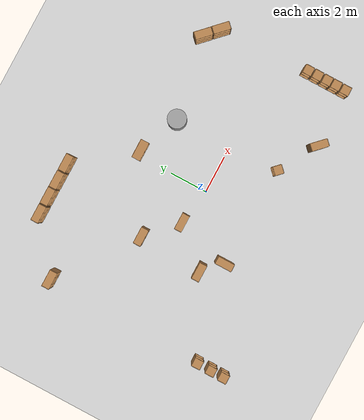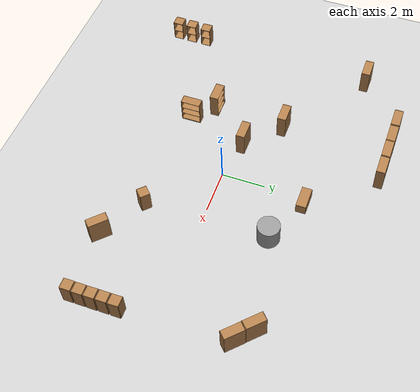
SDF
<sdf version="1.4">
 <world name="world_test_2">
  <physics type="ode">
   <real_time_update_rate>200</real_time_update_rate>
   <max_step_size>0.01</max_step_size>
   <real_time_factor>1</real_time_factor>
   <gravity>0 0 -9.8</gravity>
  </physics>
  <light name="sun" type="directional">
   <pose>0 0 10 0 -0 0</pose>
   <diffuse>0.8 0.8 0.8 1</diffuse>
   <specular>0.2 0.2 0.2 1</specular>
   <attenuation>
    <range>1000</range>
    <constant>0.9</constant>
    <linear>0.01</linear>
    <quadratic>0.001</quadratic>
   </attenuation>
   <direction>-0.5 0.1 -0.9</direction>
  </light>
  <model name="ground_plane">
   <static>1</static>
   <link name="link">
    <collision name="collision">
     <geometry><plane><normal>0 0 1</normal><size>100 100</size></plane></geometry>
     <surface><friction><ode><mu>100</mu><mu2>50</mu2></ode></friction></surface>
    </collision>
    <visual name="visual">
     <cast_shadows>0</cast_shadows>
     <geometry><plane><normal>0 0 1</normal><size>100 100</size></plane></geometry>
     <material>
      <script><uri>file://media/materials/scripts/gazebo.material</uri><name>Gazebo/Grey</name></script>
     </material>
    </visual>
    <velocity_decay><linear>0</linear><angular>0</angular></velocity_decay>
   </link>
  </model>
  <scene><ambient>0.4 0.4 0.4 1</ambient><background>0.7 0.7 0.7 1</background><shadows>1</shadows></scene>
  <model name="unit_cylinder_1_0">
   <pose>2.50227 3 0.49912 -0 -0 -3e-06</pose>
   <link name="link">
    <inertial>
     <mass>1</mass>
     <inertia><ixx>1</ixx><ixy>0</ixy><ixz>0</ixz><iyy>1</iyy><iyz>0</iyz><izz>1</izz></inertia>
    </inertial>
    <collision name="collision">
     <geometry><cylinder><radius>0.5</radius><length>1</length></cylinder></geometry>
    </collision>
    <visual name="visual">
     <geometry><cylinder><radius>0.5</radius><length>1</length></cylinder></geometry>
     <material>
      <script><uri>file://media/materials/scripts/gazebo.material</uri><name>Gazebo/Grey</name></script>
     </material>
    </visual>
    <velocity_decay><linear>0</linear><angular>0</angular></velocity_decay>
   </link>
   <static>0</static>
  </model>
  <model name="cabinet">
   <static>1</static>
   <link name="cabinet_bottom_plate">
    <inertial>
     <pose>0 0 -1 0 -0 0</pose>
     <inertia><ixx>2.05</ixx><ixy>0</ixy><ixz>0</ixz><iyy>2.05</iyy><iyz>0</iyz><izz>2.05</izz></inertia>
     <mass>25</mass>
    </inertial>
    <collision name="cabinet_bottom_plate_geom">
     <pose>0 0 0.01 0 -0 0</pose>
     <geometry><box><size>0.45 0.45 0.02</size></box></geometry>
    </collision>
    <visual name="cabinet_bottom_plate_geom_visual">
     <pose>0 0 0.01 0 -0 0</pose>
     <geometry><box><size>0.45 0.45 0.02</size></box></geometry>
     <material>
      <script><uri>file://media/materials/scripts/gazebo.material</uri><name>Gazebo/Wood</name></script>
     </material>
    </visual>
    <collision name="cabinet_bottom_plate_geom_cabinet_back_plate">
     <pose>0.235 0 0.51 0 -0 0</pose>
     <geometry><box><size>0.02 0.45 1.02</size></box></geometry>
    </collision>
    <visual name="cabinet_bottom_plate_geom_cabinet_back_plate_visual">
     <pose>0.235 0 0.51 0 -0 0</pose>
     <geometry><box><size>0.02 0.45 1.02</size></box></geometry>
     <material>
      <script><uri>file://media/materials/scripts/gazebo.material</uri><name>Gazebo/Wood</name></script>
     </material>
    </visual>
    <collision name="cabinet_bottom_plate_geom_cabinet_left_plate">
     <pose>0 0.235 0.51 0 -0 0</pose>
     <geometry><box><size>0.45 0.02 1.02</size></box></geometry>
    </collision>
    <visual name="cabinet_bottom_plate_geom_cabinet_left_plate_visual">
     <pose>0 0.235 0.51 0 -0 0</pose>
     <geometry><box><size>0.45 0.02 1.02</size></box></geometry>
     <material>
      <script><uri>file://media/materials/scripts/gazebo.material</uri><name>Gazebo/Wood</name></script>
     </material>
    </visual>
    <collision name="cabinet_bottom_plate_geom_cabinet_middle_plate">
     <pose>0 0 0.51 0 -0 0</pose>
     <geometry><box><size>0.45 0.45 0.02</size></box></geometry>
    </collision>
    <visual name="cabinet_bottom_plate_geom_cabinet_middle_plate_visual">
     <pose>0 0 0.51 0 -0 0</pose>
     <geometry><box><size>0.45 0.45 0.02</size></box></geometry>
     <material>
      <script><uri>file://media/materials/scripts/gazebo.material</uri><name>Gazebo/Wood</name></script>
     </material>
    </visual>
    <collision name="cabinet_bottom_plate_geom_cabinet_right_plate">
     <pose>0 -0.235 0.51 0 -0 0</pose>
     <geometry><box><size>0.45 0.02 1.02</size></box></geometry>
    </collision>
    <visual name="cabinet_bottom_plate_geom_cabinet_right_plate_visual">
     <pose>0 -0.235 0.51 0 -0 0</pose>
     <geometry><box><size>0.45 0.02 1.02</size></box></geometry>
     <material>
      <script><uri>file://media/materials/scripts/gazebo.material</uri><name>Gazebo/Wood</name></script>
     </material>
    </visual>
    <collision name="cabinet_bottom_plate_geom_cabinet_top_plate">
     <pose>0 0 1.01 0 -0 0</pose>
     <geometry><box><size>0.45 0.45 0.02</size></box></geometry>
    </collision>
    <visual name="cabinet_bottom_plate_geom_cabinet_top_plate_visual">
     <pose>0 0 1.01 0 -0 0</pose>
     <geometry><box><size>0.45 0.45 0.02</size></box></geometry>
     <material>
      <script><uri>file://media/materials/scripts/gazebo.material</uri><name>Gazebo/Wood</name></script>
     </material>
    </visual>
    <velocity_decay><linear>0</linear><angular>0</angular></velocity_decay>
   </link>
   <pose>2.64485 -2.64669 0 0 0 -0.785402</pose>
  </model>
  <model name="bookshelf">
   <static>1</static>
   <link name="link">
    <inertial><mass>1</mass></inertial>
    <collision name="back">
     <pose>0 0.005 0.6 0 -0 0</pose>
     <geometry><box><size>0.9 0.01 1.2</size></box></geometry>
    </collision>
    <visual name="visual1">
     <pose>0 0.005 0.6 0 -0 0</pose>
     <geometry><box><size>0.9 0.01 1.2</size></box></geometry>
     <material>
      <script><uri>file://media/materials/scripts/gazebo.material</uri><name>Gazebo/Wood</name></script>
     </material>
    </visual>
    <collision name="left_side">
     <pose>0.45 -0.195 0.6 0 -0 0</pose>
     <geometry><box><size>0.02 0.4 1.2</size></box></geometry>
    </collision>
    <visual name="visual2">
     <pose>0.45 -0.195 0.6 0 -0 0</pose>
     <geometry><box><size>0.02 0.4 1.2</size></box></geometry>
     <material>
      <script><uri>file://media/materials/scripts/gazebo.material</uri><name>Gazebo/Wood</name></script>
     </material>
    </visual>
    <collision name="right_side">
     <pose>-0.45 -0.195 0.6 0 -0 0</pose>
     <geometry><box><size>0.02 0.4 1.2</size></box></geometry>
    </collision>
    <visual name="visual3">
     <pose>-0.45 -0.195 0.6 0 -0 0</pose>
     <geometry><box><size>0.02 0.4 1.2</size></box></geometry>
     <material>
      <script><uri>file://media/materials/scripts/gazebo.material</uri><name>Gazebo/Wood</name></script>
     </material>
    </visual>
    <collision name="bottom">
     <pose>0 -0.195 0.03 0 -0 0</pose>
     <geometry><box><size>0.88 0.4 0.06</size></box></geometry>
    </collision>
    <visual name="visual4">
     <pose>0 -0.195 0.03 0 -0 0</pose>
     <geometry><box><size>0.88 0.4 0.06</size></box></geometry>
     <material>
      <script><uri>file://media/materials/scripts/gazebo.material</uri><name>Gazebo/Wood</name></script>
     </material>
    </visual>
    <collision name="top">
     <pose>0 -0.195 1.19 0 -0 0</pose>
     <geometry><box><size>0.88 0.4 0.02</size></box></geometry>
    </collision>
    <visual name="visual5">
     <pose>0 -0.195 1.19 0 -0 0</pose>
     <geometry><box><size>0.88 0.4 0.02</size></box></geometry>
     <material>
      <script><uri>file://media/materials/scripts/gazebo.material</uri><name>Gazebo/Wood</name></script>
     </material>
    </visual>
    <collision name="low_shelf">
     <pose>0 -0.195 0.43 0 -0 0</pose>
     <geometry><box><size>0.88 0.4 0.02</size></box></geometry>
    </collision>
    <visual name="visual6">
     <pose>0 -0.195 0.43 0 -0 0</pose>
     <geometry><box><size>0.88 0.4 0.02</size></box></geometry>
     <material>
      <script><uri>file://media/materials/scripts/gazebo.material</uri><name>Gazebo/Wood</name></script>
     </material>
    </visual>
    <collision name="high_shelf">
     <pose>0 -0.195 0.8 0 -0 0</pose>
     <geometry><box><size>0.88 0.4 0.02</size></box></geometry>
    </collision>
    <visual name="visual7">
     <pose>0 -0.195 0.8 0 -0 0</pose>
     <geometry><box><size>0.88 0.4 0.02</size></box></geometry>
     <material>
      <script><uri>file://media/materials/scripts/gazebo.material</uri><name>Gazebo/Wood</name></script>
     </material>
    </visual>
    <velocity_decay><linear>0</linear><angular>0</angular></velocity_decay>
   </link>
   <pose>-3.49372 1.98672 0 0 -0 0</pose>
  </model>
  <model name="bookshelf_0">
   <static>1</static>
   <link name="link">
    <inertial><mass>1</mass></inertial>
    <collision name="back">
     <pose>0 0.005 0.6 0 -0 0</pose>
     <geometry><box><size>0.9 0.01 1.2</size></box></geometry>
    </collision>
    <visual name="visual1">
     <pose>0 0.005 0.6 0 -0 0</pose>
     <geometry><box><size>0.9 0.01 1.2</size></box></geometry>
     <material>
      <script><uri>file://media/materials/scripts/gazebo.material</uri><name>Gazebo/Wood</name></script>
     </material>
    </visual>
    <collision name="left_side">
     <pose>0.45 -0.195 0.6 0 -0 0</pose>
     <geometry><box><size>0.02 0.4 1.2</size></box></geometry>
    </collision>
    <visual name="visual2">
     <pose>0.45 -0.195 0.6 0 -0 0</pose>
     <geometry><box><size>0.02 0.4 1.2</size></box></geometry>
     <material>
      <script><uri>file://media/materials/scripts/gazebo.material</uri><name>Gazebo/Wood</name></script>
     </material>
    </visual>
    <collision name="right_side">
     <pose>-0.45 -0.195 0.6 0 -0 0</pose>
     <geometry><box><size>0.02 0.4 1.2</size></box></geometry>
    </collision>
    <visual name="visual3">
     <pose>-0.45 -0.195 0.6 0 -0 0</pose>
     <geometry><box><size>0.02 0.4 1.2</size></box></geometry>
     <material>
      <script><uri>file://media/materials/scripts/gazebo.material</uri><name>Gazebo/Wood</name></script>
     </material>
    </visual>
    <collision name="bottom">
     <pose>0 -0.195 0.03 0 -0 0</pose>
     <geometry><box><size>0.88 0.4 0.06</size></box></geometry>
    </collision>
    <visual name="visual4">
     <pose>0 -0.195 0.03 0 -0 0</pose>
     <geometry><box><size>0.88 0.4 0.06</size></box></geometry>
     <material>
      <script><uri>file://media/materials/scripts/gazebo.material</uri><name>Gazebo/Wood</name></script>
     </material>
    </visual>
    <collision name="top">
     <pose>0 -0.195 1.19 0 -0 0</pose>
     <geometry><box><size>0.88 0.4 0.02</size></box></geometry>
    </collision>
    <visual name="visual5">
     <pose>0 -0.195 1.19 0 -0 0</pose>
     <geometry><box><size>0.88 0.4 0.02</size></box></geometry>
     <material>
      <script><uri>file://media/materials/scripts/gazebo.material</uri><name>Gazebo/Wood</name></script>
     </material>
    </visual>
    <collision name="low_shelf">
     <pose>0 -0.195 0.43 0 -0 0</pose>
     <geometry><box><size>0.88 0.4 0.02</size></box></geometry>
    </collision>
    <visual name="visual6">
     <pose>0 -0.195 0.43 0 -0 0</pose>
     <geometry><box><size>0.88 0.4 0.02</size></box></geometry>
     <material>
      <script><uri>file://media/materials/scripts/gazebo.material</uri><name>Gazebo/Wood</name></script>
     </material>
    </visual>
    <collision name="high_shelf">
     <pose>0 -0.195 0.8 0 -0 0</pose>
     <geometry><box><size>0.88 0.4 0.02</size></box></geometry>
    </collision>
    <visual name="visual7">
     <pose>0 -0.195 0.8 0 -0 0</pose>
     <geometry><box><size>0.88 0.4 0.02</size></box></geometry>
     <material>
      <script><uri>file://media/materials/scripts/gazebo.material</uri><name>Gazebo/Wood</name></script>
     </material>
    </visual>
    <velocity_decay><linear>0</linear><angular>0</angular></velocity_decay>
   </link>
   <pose>-2.91879 -2.51165 0 0 -0 1.5708</pose>
  </model>
  <model name="bookshelf_1">
   <static>1</static>
   <link name="link">
    <inertial><mass>1</mass></inertial>
    <collision name="back">
     <pose>0 0.005 0.6 0 -0 0</pose>
     <geometry><box><size>0.9 0.01 1.2</size></box></geometry>
    </collision>
    <visual name="visual1">
     <pose>0 0.005 0.6 0 -0 0</pose>
     <geometry><box><size>0.9 0.01 1.2</size></box></geometry>
     <material>
      <script><uri>file://media/materials/scripts/gazebo.material</uri><name>Gazebo/Wood</name></script>
     </material>
    </visual>
    <collision name="left_side">
     <pose>0.45 -0.195 0.6 0 -0 0</pose>
     <geometry><box><size>0.02 0.4 1.2</size></box></geometry>
    </collision>
    <visual name="visual2">
     <pose>0.45 -0.195 0.6 0 -0 0</pose>
     <geometry><box><size>0.02 0.4 1.2</size></box></geometry>
     <material>
      <script><uri>file://media/materials/scripts/gazebo.material</uri><name>Gazebo/Wood</name></script>
     </material>
    </visual>
    <collision name="right_side">
     <pose>-0.45 -0.195 0.6 0 -0 0</pose>
     <geometry><box><size>0.02 0.4 1.2</size></box></geometry>
    </collision>
    <visual name="visual3">
     <pose>-0.45 -0.195 0.6 0 -0 0</pose>
     <geometry><box><size>0.02 0.4 1.2</size></box></geometry>
     <material>
      <script><uri>file://media/materials/scripts/gazebo.material</uri><name>Gazebo/Wood</name></script>
     </material>
    </visual>
    <collision name="bottom">
     <pose>0 -0.195 0.03 0 -0 0</pose>
     <geometry><box><size>0.88 0.4 0.06</size></box></geometry>
    </collision>
    <visual name="visual4">
     <pose>0 -0.195 0.03 0 -0 0</pose>
     <geometry><box><size>0.88 0.4 0.06</size></box></geometry>
     <material>
      <script><uri>file://media/materials/scripts/gazebo.material</uri><name>Gazebo/Wood</name></script>
     </material>
    </visual>
    <collision name="top">
     <pose>0 -0.195 1.19 0 -0 0</pose>
     <geometry><box><size>0.88 0.4 0.02</size></box></geometry>
    </collision>
    <visual name="visual5">
     <pose>0 -0.195 1.19 0 -0 0</pose>
     <geometry><box><size>0.88 0.4 0.02</size></box></geometry>
     <material>
      <script><uri>file://media/materials/scripts/gazebo.material</uri><name>Gazebo/Wood</name></script>
     </material>
    </visual>
    <collision name="low_shelf">
     <pose>0 -0.195 0.43 0 -0 0</pose>
     <geometry><box><size>0.88 0.4 0.02</size></box></geometry>
    </collision>
    <visual name="visual6">
     <pose>0 -0.195 0.43 0 -0 0</pose>
     <geometry><box><size>0.88 0.4 0.02</size></box></geometry>
     <material>
      <script><uri>file://media/materials/scripts/gazebo.material</uri><name>Gazebo/Wood</name></script>
     </material>
    </visual>
    <collision name="high_shelf">
     <pose>0 -0.195 0.8 0 -0 0</pose>
     <geometry><box><size>0.88 0.4 0.02</size></box></geometry>
    </collision>
    <visual name="visual7">
     <pose>0 -0.195 0.8 0 -0 0</pose>
     <geometry><box><size>0.88 0.4 0.02</size></box></geometry>
     <material>
      <script><uri>file://media/materials/scripts/gazebo.material</uri><name>Gazebo/Wood</name></script>
     </material>
    </visual>
    <velocity_decay><linear>0</linear><angular>0</angular></velocity_decay>
   </link>
   <pose>-7.50696 4.96643 0 0 -0 0</pose>
  </model>
  <model name="bookshelf_2">
   <static>1</static>
   <link name="link">
    <inertial><mass>1</mass></inertial>
    <collision name="back">
     <pose>0 0.005 0.6 0 -0 0</pose>
     <geometry><box><size>0.9 0.01 1.2</size></box></geometry>
    </collision>
    <visual name="visual1">
     <pose>0 0.005 0.6 0 -0 0</pose>
     <geometry><box><size>0.9 0.01 1.2</size></box></geometry>
     <material>
      <script><uri>file://media/materials/scripts/gazebo.material</uri><name>Gazebo/Wood</name></script>
     </material>
    </visual>
    <collision name="left_side">
     <pose>0.45 -0.195 0.6 0 -0 0</pose>
     <geometry><box><size>0.02 0.4 1.2</size></box></geometry>
    </collision>
    <visual name="visual2">
     <pose>0.45 -0.195 0.6 0 -0 0</pose>
     <geometry><box><size>0.02 0.4 1.2</size></box></geometry>
     <material>
      <script><uri>file://media/materials/scripts/gazebo.material</uri><name>Gazebo/Wood</name></script>
     </material>
    </visual>
    <collision name="right_side">
     <pose>-0.45 -0.195 0.6 0 -0 0</pose>
     <geometry><box><size>0.02 0.4 1.2</size></box></geometry>
    </collision>
    <visual name="visual3">
     <pose>-0.45 -0.195 0.6 0 -0 0</pose>
     <geometry><box><size>0.02 0.4 1.2</size></box></geometry>
     <material>
      <script><uri>file://media/materials/scripts/gazebo.material</uri><name>Gazebo/Wood</name></script>
     </material>
    </visual>
    <collision name="bottom">
     <pose>0 -0.195 0.03 0 -0 0</pose>
     <geometry><box><size>0.88 0.4 0.06</size></box></geometry>
    </collision>
    <visual name="visual4">
     <pose>0 -0.195 0.03 0 -0 0</pose>
     <geometry><box><size>0.88 0.4 0.06</size></box></geometry>
     <material>
      <script><uri>file://media/materials/scripts/gazebo.material</uri><name>Gazebo/Wood</name></script>
     </material>
    </visual>
    <collision name="top">
     <pose>0 -0.195 1.19 0 -0 0</pose>
     <geometry><box><size>0.88 0.4 0.02</size></box></geometry>
    </collision>
    <visual name="visual5">
     <pose>0 -0.195 1.19 0 -0 0</pose>
     <geometry><box><size>0.88 0.4 0.02</size></box></geometry>
     <material>
      <script><uri>file://media/materials/scripts/gazebo.material</uri><name>Gazebo/Wood</name></script>
     </material>
    </visual>
    <collision name="low_shelf">
     <pose>0 -0.195 0.43 0 -0 0</pose>
     <geometry><box><size>0.88 0.4 0.02</size></box></geometry>
    </collision>
    <visual name="visual6">
     <pose>0 -0.195 0.43 0 -0 0</pose>
     <geometry><box><size>0.88 0.4 0.02</size></box></geometry>
     <material>
      <script><uri>file://media/materials/scripts/gazebo.material</uri><name>Gazebo/Wood</name></script>
     </material>
    </visual>
    <collision name="high_shelf">
     <pose>0 -0.195 0.8 0 -0 0</pose>
     <geometry><box><size>0.88 0.4 0.02</size></box></geometry>
    </collision>
    <visual name="visual7">
     <pose>0 -0.195 0.8 0 -0 0</pose>
     <geometry><box><size>0.88 0.4 0.02</size></box></geometry>
     <material>
      <script><uri>file://media/materials/scripts/gazebo.material</uri><name>Gazebo/Wood</name></script>
     </material>
    </visual>
    <velocity_decay><linear>0</linear><angular>0</angular></velocity_decay>
   </link>
   <pose>-3.67626 -1.78554 0 0 0 -3.14159</pose>
  </model>
  <model name="cabinet_1">
   <static>1</static>
   <link name="cabinet_bottom_plate">
    <inertial>
     <pose>0 0 -1 0 -0 0</pose>
     <inertia><ixx>2.05</ixx><ixy>0</ixy><ixz>0</ixz><iyy>2.05</iyy><iyz>0</iyz><izz>2.05</izz></inertia>
     <mass>25</mass>
    </inertial>
    <collision name="cabinet_bottom_plate_geom">
     <pose>0 0 0.01 0 -0 0</pose>
     <geometry><box><size>0.45 0.45 0.02</size></box></geometry>
    </collision>
    <visual name="cabinet_bottom_plate_geom_visual">
     <pose>0 0 0.01 0 -0 0</pose>
     <geometry><box><size>0.45 0.45 0.02</size></box></geometry>
     <material>
      <script><uri>file://media/materials/scripts/gazebo.material</uri><name>Gazebo/Wood</name></script>
     </material>
    </visual>
    <collision name="cabinet_bottom_plate_geom_cabinet_back_plate">
     <pose>0.235 0 0.51 0 -0 0</pose>
     <geometry><box><size>0.02 0.45 1.02</size></box></geometry>
    </collision>
    <visual name="cabinet_bottom_plate_geom_cabinet_back_plate_visual">
     <pose>0.235 0 0.51 0 -0 0</pose>
     <geometry><box><size>0.02 0.45 1.02</size></box></geometry>
     <material>
      <script><uri>file://media/materials/scripts/gazebo.material</uri><name>Gazebo/Wood</name></script>
     </material>
    </visual>
    <collision name="cabinet_bottom_plate_geom_cabinet_left_plate">
     <pose>0 0.235 0.51 0 -0 0</pose>
     <geometry><box><size>0.45 0.02 1.02</size></box></geometry>
    </collision>
    <visual name="cabinet_bottom_plate_geom_cabinet_left_plate_visual">
     <pose>0 0.235 0.51 0 -0 0</pose>
     <geometry><box><size>0.45 0.02 1.02</size></box></geometry>
     <material>
      <script><uri>file://media/materials/scripts/gazebo.material</uri><name>Gazebo/Wood</name></script>
     </material>
    </visual>
    <collision name="cabinet_bottom_plate_geom_cabinet_middle_plate">
     <pose>0 0 0.51 0 -0 0</pose>
     <geometry><box><size>0.45 0.45 0.02</size></box></geometry>
    </collision>
    <visual name="cabinet_bottom_plate_geom_cabinet_middle_plate_visual">
     <pose>0 0 0.51 0 -0 0</pose>
     <geometry><box><size>0.45 0.45 0.02</size></box></geometry>
     <material>
      <script><uri>file://media/materials/scripts/gazebo.material</uri><name>Gazebo/Wood</name></script>
     </material>
    </visual>
    <collision name="cabinet_bottom_plate_geom_cabinet_right_plate">
     <pose>0 -0.235 0.51 0 -0 0</pose>
     <geometry><box><size>0.45 0.02 1.02</size></box></geometry>
    </collision>
    <visual name="cabinet_bottom_plate_geom_cabinet_right_plate_visual">
     <pose>0 -0.235 0.51 0 -0 0</pose>
     <geometry><box><size>0.45 0.02 1.02</size></box></geometry>
     <material>
      <script><uri>file://media/materials/scripts/gazebo.material</uri><name>Gazebo/Wood</name></script>
     </material>
    </visual>
    <collision name="cabinet_bottom_plate_geom_cabinet_top_plate">
     <pose>0 0 1.01 0 -0 0</pose>
     <geometry><box><size>0.45 0.45 0.02</size></box></geometry>
    </collision>
    <visual name="cabinet_bottom_plate_geom_cabinet_top_plate_visual">
     <pose>0 0 1.01 0 -0 0</pose>
     <geometry><box><size>0.45 0.45 0.02</size></box></geometry>
     <material>
      <script><uri>file://media/materials/scripts/gazebo.material</uri><name>Gazebo/Wood</name></script>
     </material>
    </visual>
    <velocity_decay><linear>0</linear><angular>0</angular></velocity_decay>
   </link>
   <pose>7.73323 -2.6778 0 0 -0 0</pose>
  </model>
  <model name="cabinet_2">
   <static>1</static>
   <link name="cabinet_bottom_plate">
    <inertial>
     <pose>0 0 -1 0 -0 0</pose>
     <inertia><ixx>2.05</ixx><ixy>0</ixy><ixz>0</ixz><iyy>2.05</iyy><iyz>0</iyz><izz>2.05</izz></inertia>
     <mass>25</mass>
    </inertial>
    <collision name="cabinet_bottom_plate_geom">
     <pose>0 0 0.01 0 -0 0</pose>
     <geometry><box><size>0.45 0.45 0.02</size></box></geometry>
    </collision>
    <visual name="cabinet_bottom_plate_geom_visual">
     <pose>0 0 0.01 0 -0 0</pose>
     <geometry><box><size>0.45 0.45 0.02</size></box></geometry>
     <material>
      <script><uri>file://media/materials/scripts/gazebo.material</uri><name>Gazebo/Wood</name></script>
     </material>
    </visual>
    <collision name="cabinet_bottom_plate_geom_cabinet_back_plate">
     <pose>0.235 0 0.51 0 -0 0</pose>
     <geometry><box><size>0.02 0.45 1.02</size></box></geometry>
    </collision>
    <visual name="cabinet_bottom_plate_geom_cabinet_back_plate_visual">
     <pose>0.235 0 0.51 0 -0 0</pose>
     <geometry><box><size>0.02 0.45 1.02</size></box></geometry>
     <material>
      <script><uri>file://media/materials/scripts/gazebo.material</uri><name>Gazebo/Wood</name></script>
     </material>
    </visual>
    <collision name="cabinet_bottom_plate_geom_cabinet_left_plate">
     <pose>0 0.235 0.51 0 -0 0</pose>
     <geometry><box><size>0.45 0.02 1.02</size></box></geometry>
    </collision>
    <visual name="cabinet_bottom_plate_geom_cabinet_left_plate_visual">
     <pose>0 0.235 0.51 0 -0 0</pose>
     <geometry><box><size>0.45 0.02 1.02</size></box></geometry>
     <material>
      <script><uri>file://media/materials/scripts/gazebo.material</uri><name>Gazebo/Wood</name></script>
     </material>
    </visual>
    <collision name="cabinet_bottom_plate_geom_cabinet_middle_plate">
     <pose>0 0 0.51 0 -0 0</pose>
     <geometry><box><size>0.45 0.45 0.02</size></box></geometry>
    </collision>
    <visual name="cabinet_bottom_plate_geom_cabinet_middle_plate_visual">
     <pose>0 0 0.51 0 -0 0</pose>
     <geometry><box><size>0.45 0.45 0.02</size></box></geometry>
     <material>
      <script><uri>file://media/materials/scripts/gazebo.material</uri><name>Gazebo/Wood</name></script>
     </material>
    </visual>
    <collision name="cabinet_bottom_plate_geom_cabinet_right_plate">
     <pose>0 -0.235 0.51 0 -0 0</pose>
     <geometry><box><size>0.45 0.02 1.02</size></box></geometry>
    </collision>
    <visual name="cabinet_bottom_plate_geom_cabinet_right_plate_visual">
     <pose>0 -0.235 0.51 0 -0 0</pose>
     <geometry><box><size>0.45 0.02 1.02</size></box></geometry>
     <material>
      <script><uri>file://media/materials/scripts/gazebo.material</uri><name>Gazebo/Wood</name></script>
     </material>
    </visual>
    <collision name="cabinet_bottom_plate_geom_cabinet_top_plate">
     <pose>0 0 1.01 0 -0 0</pose>
     <geometry><box><size>0.45 0.45 0.02</size></box></geometry>
    </collision>
    <visual name="cabinet_bottom_plate_geom_cabinet_top_plate_visual">
     <pose>0 0 1.01 0 -0 0</pose>
     <geometry><box><size>0.45 0.45 0.02</size></box></geometry>
     <material>
      <script><uri>file://media/materials/scripts/gazebo.material</uri><name>Gazebo/Wood</name></script>
     </material>
    </visual>
    <velocity_decay><linear>0</linear><angular>0</angular></velocity_decay>
   </link>
   <pose>7.73111 -2.14886 0 0 -0 0</pose>
  </model>
  <model name="cabinet_3">
   <static>1</static>
   <link name="cabinet_bottom_plate">
    <inertial>
     <pose>0 0 -1 0 -0 0</pose>
     <inertia><ixx>2.05</ixx><ixy>0</ixy><ixz>0</ixz><iyy>2.05</iyy><iyz>0</iyz><izz>2.05</izz></inertia>
     <mass>25</mass>
    </inertial>
    <collision name="cabinet_bottom_plate_geom">
     <pose>0 0 0.01 0 -0 0</pose>
     <geometry><box><size>0.45 0.45 0.02</size></box></geometry>
    </collision>
    <visual name="cabinet_bottom_plate_geom_visual">
     <pose>0 0 0.01 0 -0 0</pose>
     <geometry><box><size>0.45 0.45 0.02</size></box></geometry>
     <material>
      <script><uri>file://media/materials/scripts/gazebo.material</uri><name>Gazebo/Wood</name></script>
     </material>
    </visual>
    <collision name="cabinet_bottom_plate_geom_cabinet_back_plate">
     <pose>0.235 0 0.51 0 -0 0</pose>
     <geometry><box><size>0.02 0.45 1.02</size></box></geometry>
    </collision>
    <visual name="cabinet_bottom_plate_geom_cabinet_back_plate_visual">
     <pose>0.235 0 0.51 0 -0 0</pose>
     <geometry><box><size>0.02 0.45 1.02</size></box></geometry>
     <material>
      <script><uri>file://media/materials/scripts/gazebo.material</uri><name>Gazebo/Wood</name></script>
     </material>
    </visual>
    <collision name="cabinet_bottom_plate_geom_cabinet_left_plate">
     <pose>0 0.235 0.51 0 -0 0</pose>
     <geometry><box><size>0.45 0.02 1.02</size></box></geometry>
    </collision>
    <visual name="cabinet_bottom_plate_geom_cabinet_left_plate_visual">
     <pose>0 0.235 0.51 0 -0 0</pose>
     <geometry><box><size>0.45 0.02 1.02</size></box></geometry>
     <material>
      <script><uri>file://media/materials/scripts/gazebo.material</uri><name>Gazebo/Wood</name></script>
     </material>
    </visual>
    <collision name="cabinet_bottom_plate_geom_cabinet_middle_plate">
     <pose>0 0 0.51 0 -0 0</pose>
     <geometry><box><size>0.45 0.45 0.02</size></box></geometry>
    </collision>
    <visual name="cabinet_bottom_plate_geom_cabinet_middle_plate_visual">
     <pose>0 0 0.51 0 -0 0</pose>
     <geometry><box><size>0.45 0.45 0.02</size></box></geometry>
     <material>
      <script><uri>file://media/materials/scripts/gazebo.material</uri><name>Gazebo/Wood</name></script>
     </material>
    </visual>
    <collision name="cabinet_bottom_plate_geom_cabinet_right_plate">
     <pose>0 -0.235 0.51 0 -0 0</pose>
     <geometry><box><size>0.45 0.02 1.02</size></box></geometry>
    </collision>
    <visual name="cabinet_bottom_plate_geom_cabinet_right_plate_visual">
     <pose>0 -0.235 0.51 0 -0 0</pose>
     <geometry><box><size>0.45 0.02 1.02</size></box></geometry>
     <material>
      <script><uri>file://media/materials/scripts/gazebo.material</uri><name>Gazebo/Wood</name></script>
     </material>
    </visual>
    <collision name="cabinet_bottom_plate_geom_cabinet_top_plate">
     <pose>0 0 1.01 0 -0 0</pose>
     <geometry><box><size>0.45 0.45 0.02</size></box></geometry>
    </collision>
    <visual name="cabinet_bottom_plate_geom_cabinet_top_plate_visual">
     <pose>0 0 1.01 0 -0 0</pose>
     <geometry><box><size>0.45 0.45 0.02</size></box></geometry>
     <material>
      <script><uri>file://media/materials/scripts/gazebo.material</uri><name>Gazebo/Wood</name></script>
     </material>
    </visual>
    <velocity_decay><linear>0</linear><angular>0</angular></velocity_decay>
   </link>
   <pose>7.72799 -1.62137 0 0 -0 0</pose>
  </model>
  <model name="bookshelf_3">
   <static>1</static>
   <link name="link">
    <inertial><mass>1</mass></inertial>
    <collision name="back">
     <pose>0 0.005 0.6 0 -0 0</pose>
     <geometry><box><size>0.9 0.01 1.2</size></box></geometry>
    </collision>
    <visual name="visual1">
     <pose>0 0.005 0.6 0 -0 0</pose>
     <geometry><box><size>0.9 0.01 1.2</size></box></geometry>
     <material>
      <script><uri>file://media/materials/scripts/gazebo.material</uri><name>Gazebo/Wood</name></script>
     </material>
    </visual>
    <collision name="left_side">
     <pose>0.45 -0.195 0.6 0 -0 0</pose>
     <geometry><box><size>0.02 0.4 1.2</size></box></geometry>
    </collision>
    <visual name="visual2">
     <pose>0.45 -0.195 0.6 0 -0 0</pose>
     <geometry><box><size>0.02 0.4 1.2</size></box></geometry>
     <material>
      <script><uri>file://media/materials/scripts/gazebo.material</uri><name>Gazebo/Wood</name></script>
     </material>
    </visual>
    <collision name="right_side">
     <pose>-0.45 -0.195 0.6 0 -0 0</pose>
     <geometry><box><size>0.02 0.4 1.2</size></box></geometry>
    </collision>
    <visual name="visual3">
     <pose>-0.45 -0.195 0.6 0 -0 0</pose>
     <geometry><box><size>0.02 0.4 1.2</size></box></geometry>
     <material>
      <script><uri>file://media/materials/scripts/gazebo.material</uri><name>Gazebo/Wood</name></script>
     </material>
    </visual>
    <collision name="bottom">
     <pose>0 -0.195 0.03 0 -0 0</pose>
     <geometry><box><size>0.88 0.4 0.06</size></box></geometry>
    </collision>
    <visual name="visual4">
     <pose>0 -0.195 0.03 0 -0 0</pose>
     <geometry><box><size>0.88 0.4 0.06</size></box></geometry>
     <material>
      <script><uri>file://media/materials/scripts/gazebo.material</uri><name>Gazebo/Wood</name></script>
     </material>
    </visual>
    <collision name="top">
     <pose>0 -0.195 1.19 0 -0 0</pose>
     <geometry><box><size>0.88 0.4 0.02</size></box></geometry>
    </collision>
    <visual name="visual5">
     <pose>0 -0.195 1.19 0 -0 0</pose>
     <geometry><box><size>0.88 0.4 0.02</size></box></geometry>
     <material>
      <script><uri>file://media/materials/scripts/gazebo.material</uri><name>Gazebo/Wood</name></script>
     </material>
    </visual>
    <collision name="low_shelf">
     <pose>0 -0.195 0.43 0 -0 0</pose>
     <geometry><box><size>0.88 0.4 0.02</size></box></geometry>
    </collision>
    <visual name="visual6">
     <pose>0 -0.195 0.43 0 -0 0</pose>
     <geometry><box><size>0.88 0.4 0.02</size></box></geometry>
     <material>
      <script><uri>file://media/materials/scripts/gazebo.material</uri><name>Gazebo/Wood</name></script>
     </material>
    </visual>
    <collision name="high_shelf">
     <pose>0 -0.195 0.8 0 -0 0</pose>
     <geometry><box><size>0.88 0.4 0.02</size></box></geometry>
    </collision>
    <visual name="visual7">
     <pose>0 -0.195 0.8 0 -0 0</pose>
     <geometry><box><size>0.88 0.4 0.02</size></box></geometry>
     <material>
      <script><uri>file://media/materials/scripts/gazebo.material</uri><name>Gazebo/Wood</name></script>
     </material>
    </visual>
    <velocity_decay><linear>0</linear><angular>0</angular></velocity_decay>
   </link>
   <pose>-2.04759 6.98349 0 0 -0 0</pose>
  </model>
  <model name="bookshelf_4">
   <static>1</static>
   <link name="link">
    <inertial><mass>1</mass></inertial>
    <collision name="back">
     <pose>0 0.005 0.6 0 -0 0</pose>
     <geometry><box><size>0.9 0.01 1.2</size></box></geometry>
    </collision>
    <visual name="visual1">
     <pose>0 0.005 0.6 0 -0 0</pose>
     <geometry><box><size>0.9 0.01 1.2</size></box></geometry>
     <material>
      <script><uri>file://media/materials/scripts/gazebo.material</uri><name>Gazebo/Wood</name></script>
     </material>
    </visual>
    <collision name="left_side">
     <pose>0.45 -0.195 0.6 0 -0 0</pose>
     <geometry><box><size>0.02 0.4 1.2</size></box></geometry>
    </collision>
    <visual name="visual2">
     <pose>0.45 -0.195 0.6 0 -0 0</pose>
     <geometry><box><size>0.02 0.4 1.2</size></box></geometry>
     <material>
      <script><uri>file://media/materials/scripts/gazebo.material</uri><name>Gazebo/Wood</name></script>
     </material>
    </visual>
    <collision name="right_side">
     <pose>-0.45 -0.195 0.6 0 -0 0</pose>
     <geometry><box><size>0.02 0.4 1.2</size></box></geometry>
    </collision>
    <visual name="visual3">
     <pose>-0.45 -0.195 0.6 0 -0 0</pose>
     <geometry><box><size>0.02 0.4 1.2</size></box></geometry>
     <material>
      <script><uri>file://media/materials/scripts/gazebo.material</uri><name>Gazebo/Wood</name></script>
     </material>
    </visual>
    <collision name="bottom">
     <pose>0 -0.195 0.03 0 -0 0</pose>
     <geometry><box><size>0.88 0.4 0.06</size></box></geometry>
    </collision>
    <visual name="visual4">
     <pose>0 -0.195 0.03 0 -0 0</pose>
     <geometry><box><size>0.88 0.4 0.06</size></box></geometry>
     <material>
      <script><uri>file://media/materials/scripts/gazebo.material</uri><name>Gazebo/Wood</name></script>
     </material>
    </visual>
    <collision name="top">
     <pose>0 -0.195 1.19 0 -0 0</pose>
     <geometry><box><size>0.88 0.4 0.02</size></box></geometry>
    </collision>
    <visual name="visual5">
     <pose>0 -0.195 1.19 0 -0 0</pose>
     <geometry><box><size>0.88 0.4 0.02</size></box></geometry>
     <material>
      <script><uri>file://media/materials/scripts/gazebo.material</uri><name>Gazebo/Wood</name></script>
     </material>
    </visual>
    <collision name="low_shelf">
     <pose>0 -0.195 0.43 0 -0 0</pose>
     <geometry><box><size>0.88 0.4 0.02</size></box></geometry>
    </collision>
    <visual name="visual6">
     <pose>0 -0.195 0.43 0 -0 0</pose>
     <geometry><box><size>0.88 0.4 0.02</size></box></geometry>
     <material>
      <script><uri>file://media/materials/scripts/gazebo.material</uri><name>Gazebo/Wood</name></script>
     </material>
    </visual>
    <collision name="high_shelf">
     <pose>0 -0.195 0.8 0 -0 0</pose>
     <geometry><box><size>0.88 0.4 0.02</size></box></geometry>
    </collision>
    <visual name="visual7">
     <pose>0 -0.195 0.8 0 -0 0</pose>
     <geometry><box><size>0.88 0.4 0.02</size></box></geometry>
     <material>
      <script><uri>file://media/materials/scripts/gazebo.material</uri><name>Gazebo/Wood</name></script>
     </material>
    </visual>
    <velocity_decay><linear>0</linear><angular>0</angular></velocity_decay>
   </link>
   <pose>-2.99588 6.98711 0 0 -0 0</pose>
  </model>
  <model name="bookshelf_5">
   <static>1</static>
   <link name="link">
    <inertial><mass>1</mass></inertial>
    <collision name="back">
     <pose>0 0.005 0.6 0 -0 0</pose>
     <geometry><box><size>0.9 0.01 1.2</size></box></geometry>
    </collision>
    <visual name="visual1">
     <pose>0 0.005 0.6 0 -0 0</pose>
     <geometry><box><size>0.9 0.01 1.2</size></box></geometry>
     <material>
      <script><uri>file://media/materials/scripts/gazebo.material</uri><name>Gazebo/Wood</name></script>
     </material>
    </visual>
    <collision name="left_side">
     <pose>0.45 -0.195 0.6 0 -0 0</pose>
     <geometry><box><size>0.02 0.4 1.2</size></box></geometry>
    </collision>
    <visual name="visual2">
     <pose>0.45 -0.195 0.6 0 -0 0</pose>
     <geometry><box><size>0.02 0.4 1.2</size></box></geometry>
     <material>
      <script><uri>file://media/materials/scripts/gazebo.material</uri><name>Gazebo/Wood</name></script>
     </material>
    </visual>
    <collision name="right_side">
     <pose>-0.45 -0.195 0.6 0 -0 0</pose>
     <geometry><box><size>0.02 0.4 1.2</size></box></geometry>
    </collision>
    <visual name="visual3">
     <pose>-0.45 -0.195 0.6 0 -0 0</pose>
     <geometry><box><size>0.02 0.4 1.2</size></box></geometry>
     <material>
      <script><uri>file://media/materials/scripts/gazebo.material</uri><name>Gazebo/Wood</name></script>
     </material>
    </visual>
    <collision name="bottom">
     <pose>0 -0.195 0.03 0 -0 0</pose>
     <geometry><box><size>0.88 0.4 0.06</size></box></geometry>
    </collision>
    <visual name="visual4">
     <pose>0 -0.195 0.03 0 -0 0</pose>
     <geometry><box><size>0.88 0.4 0.06</size></box></geometry>
     <material>
      <script><uri>file://media/materials/scripts/gazebo.material</uri><name>Gazebo/Wood</name></script>
     </material>
    </visual>
    <collision name="top">
     <pose>0 -0.195 1.19 0 -0 0</pose>
     <geometry><box><size>0.88 0.4 0.02</size></box></geometry>
    </collision>
    <visual name="visual5">
     <pose>0 -0.195 1.19 0 -0 0</pose>
     <geometry><box><size>0.88 0.4 0.02</size></box></geometry>
     <material>
      <script><uri>file://media/materials/scripts/gazebo.material</uri><name>Gazebo/Wood</name></script>
     </material>
    </visual>
    <collision name="low_shelf">
     <pose>0 -0.195 0.43 0 -0 0</pose>
     <geometry><box><size>0.88 0.4 0.02</size></box></geometry>
    </collision>
    <visual name="visual6">
     <pose>0 -0.195 0.43 0 -0 0</pose>
     <geometry><box><size>0.88 0.4 0.02</size></box></geometry>
     <material>
      <script><uri>file://media/materials/scripts/gazebo.material</uri><name>Gazebo/Wood</name></script>
     </material>
    </visual>
    <collision name="high_shelf">
     <pose>0 -0.195 0.8 0 -0 0</pose>
     <geometry><box><size>0.88 0.4 0.02</size></box></geometry>
    </collision>
    <visual name="visual7">
     <pose>0 -0.195 0.8 0 -0 0</pose>
     <geometry><box><size>0.88 0.4 0.02</size></box></geometry>
     <material>
      <script><uri>file://media/materials/scripts/gazebo.material</uri><name>Gazebo/Wood</name></script>
     </material>
    </visual>
    <velocity_decay><linear>0</linear><angular>0</angular></velocity_decay>
   </link>
   <pose>-3.92684 6.99296 0 0 -0 0</pose>
  </model>
  <model name="bookshelf_6">
   <static>1</static>
   <link name="link">
    <inertial><mass>1</mass></inertial>
    <collision name="back">
     <pose>0 0.005 0.6 0 -0 0</pose>
     <geometry><box><size>0.9 0.01 1.2</size></box></geometry>
    </collision>
    <visual name="visual1">
     <pose>0 0.005 0.6 0 -0 0</pose>
     <geometry><box><size>0.9 0.01 1.2</size></box></geometry>
     <material>
      <script><uri>file://media/materials/scripts/gazebo.material</uri><name>Gazebo/Wood</name></script>
     </material>
    </visual>
    <collision name="left_side">
     <pose>0.45 -0.195 0.6 0 -0 0</pose>
     <geometry><box><size>0.02 0.4 1.2</size></box></geometry>
    </collision>
    <visual name="visual2">
     <pose>0.45 -0.195 0.6 0 -0 0</pose>
     <geometry><box><size>0.02 0.4 1.2</size></box></geometry>
     <material>
      <script><uri>file://media/materials/scripts/gazebo.material</uri><name>Gazebo/Wood</name></script>
     </material>
    </visual>
    <collision name="right_side">
     <pose>-0.45 -0.195 0.6 0 -0 0</pose>
     <geometry><box><size>0.02 0.4 1.2</size></box></geometry>
    </collision>
    <visual name="visual3">
     <pose>-0.45 -0.195 0.6 0 -0 0</pose>
     <geometry><box><size>0.02 0.4 1.2</size></box></geometry>
     <material>
      <script><uri>file://media/materials/scripts/gazebo.material</uri><name>Gazebo/Wood</name></script>
     </material>
    </visual>
    <collision name="bottom">
     <pose>0 -0.195 0.03 0 -0 0</pose>
     <geometry><box><size>0.88 0.4 0.06</size></box></geometry>
    </collision>
    <visual name="visual4">
     <pose>0 -0.195 0.03 0 -0 0</pose>
     <geometry><box><size>0.88 0.4 0.06</size></box></geometry>
     <material>
      <script><uri>file://media/materials/scripts/gazebo.material</uri><name>Gazebo/Wood</name></script>
     </material>
    </visual>
    <collision name="top">
     <pose>0 -0.195 1.19 0 -0 0</pose>
     <geometry><box><size>0.88 0.4 0.02</size></box></geometry>
    </collision>
    <visual name="visual5">
     <pose>0 -0.195 1.19 0 -0 0</pose>
     <geometry><box><size>0.88 0.4 0.02</size></box></geometry>
     <material>
      <script><uri>file://media/materials/scripts/gazebo.material</uri><name>Gazebo/Wood</name></script>
     </material>
    </visual>
    <collision name="low_shelf">
     <pose>0 -0.195 0.43 0 -0 0</pose>
     <geometry><box><size>0.88 0.4 0.02</size></box></geometry>
    </collision>
    <visual name="visual6">
     <pose>0 -0.195 0.43 0 -0 0</pose>
     <geometry><box><size>0.88 0.4 0.02</size></box></geometry>
     <material>
      <script><uri>file://media/materials/scripts/gazebo.material</uri><name>Gazebo/Wood</name></script>
     </material>
    </visual>
    <collision name="high_shelf">
     <pose>0 -0.195 0.8 0 -0 0</pose>
     <geometry><box><size>0.88 0.4 0.02</size></box></geometry>
    </collision>
    <visual name="visual7">
     <pose>0 -0.195 0.8 0 -0 0</pose>
     <geometry><box><size>0.88 0.4 0.02</size></box></geometry>
     <material>
      <script><uri>file://media/materials/scripts/gazebo.material</uri><name>Gazebo/Wood</name></script>
     </material>
    </visual>
    <velocity_decay><linear>0</linear><angular>0</angular></velocity_decay>
   </link>
   <pose>-4.88305 6.99057 0 0 -0 0</pose>
  </model>
  <model name="cabinet_5">
   <static>1</static>
   <link name="cabinet_bottom_plate">
    <inertial>
     <pose>0 0 -1 0 -0 0</pose>
     <inertia><ixx>2.05</ixx><ixy>0</ixy><ixz>0</ixz><iyy>2.05</iyy><iyz>0</iyz><izz>2.05</izz></inertia>
     <mass>25</mass>
    </inertial>
    <collision name="cabinet_bottom_plate_geom">
     <pose>0 0 0.01 0 -0 0</pose>
     <geometry><box><size>0.45 0.45 0.02</size></box></geometry>
    </collision>
    <visual name="cabinet_bottom_plate_geom_visual">
     <pose>0 0 0.01 0 -0 0</pose>
     <geometry><box><size>0.45 0.45 0.02</size></box></geometry>
     <material>
      <script><uri>file://media/materials/scripts/gazebo.material</uri><name>Gazebo/Wood</name></script>
     </material>
    </visual>
    <collision name="cabinet_bottom_plate_geom_cabinet_back_plate">
     <pose>0.235 0 0.51 0 -0 0</pose>
     <geometry><box><size>0.02 0.45 1.02</size></box></geometry>
    </collision>
    <visual name="cabinet_bottom_plate_geom_cabinet_back_plate_visual">
     <pose>0.235 0 0.51 0 -0 0</pose>
     <geometry><box><size>0.02 0.45 1.02</size></box></geometry>
     <material>
      <script><uri>file://media/materials/scripts/gazebo.material</uri><name>Gazebo/Wood</name></script>
     </material>
    </visual>
    <collision name="cabinet_bottom_plate_geom_cabinet_left_plate">
     <pose>0 0.235 0.51 0 -0 0</pose>
     <geometry><box><size>0.45 0.02 1.02</size></box></geometry>
    </collision>
    <visual name="cabinet_bottom_plate_geom_cabinet_left_plate_visual">
     <pose>0 0.235 0.51 0 -0 0</pose>
     <geometry><box><size>0.45 0.02 1.02</size></box></geometry>
     <material>
      <script><uri>file://media/materials/scripts/gazebo.material</uri><name>Gazebo/Wood</name></script>
     </material>
    </visual>
    <collision name="cabinet_bottom_plate_geom_cabinet_middle_plate">
     <pose>0 0 0.51 0 -0 0</pose>
     <geometry><box><size>0.45 0.45 0.02</size></box></geometry>
    </collision>
    <visual name="cabinet_bottom_plate_geom_cabinet_middle_plate_visual">
     <pose>0 0 0.51 0 -0 0</pose>
     <geometry><box><size>0.45 0.45 0.02</size></box></geometry>
     <material>
      <script><uri>file://media/materials/scripts/gazebo.material</uri><name>Gazebo/Wood</name></script>
     </material>
    </visual>
    <collision name="cabinet_bottom_plate_geom_cabinet_right_plate">
     <pose>0 -0.235 0.51 0 -0 0</pose>
     <geometry><box><size>0.45 0.02 1.02</size></box></geometry>
    </collision>
    <visual name="cabinet_bottom_plate_geom_cabinet_right_plate_visual">
     <pose>0 -0.235 0.51 0 -0 0</pose>
     <geometry><box><size>0.45 0.02 1.02</size></box></geometry>
     <material>
      <script><uri>file://media/materials/scripts/gazebo.material</uri><name>Gazebo/Wood</name></script>
     </material>
    </visual>
    <collision name="cabinet_bottom_plate_geom_cabinet_top_plate">
     <pose>0 0 1.01 0 -0 0</pose>
     <geometry><box><size>0.45 0.45 0.02</size></box></geometry>
    </collision>
    <visual name="cabinet_bottom_plate_geom_cabinet_top_plate_visual">
     <pose>0 0 1.01 0 -0 0</pose>
     <geometry><box><size>0.45 0.45 0.02</size></box></geometry>
     <material>
      <script><uri>file://media/materials/scripts/gazebo.material</uri><name>Gazebo/Wood</name></script>
     </material>
    </visual>
    <velocity_decay><linear>0</linear><angular>0</angular></velocity_decay>
   </link>
   <pose>7.73486 -3.19267 0 0 -0 0</pose>
  </model>
  <model name="cabinet_6">
   <static>1</static>
   <link name="cabinet_bottom_plate">
    <inertial>
     <pose>0 0 -1 0 -0 0</pose>
     <inertia><ixx>2.05</ixx><ixy>0</ixy><ixz>0</ixz><iyy>2.05</iyy><iyz>0</iyz><izz>2.05</izz></inertia>
     <mass>25</mass>
    </inertial>
    <collision name="cabinet_bottom_plate_geom">
     <pose>0 0 0.01 0 -0 0</pose>
     <geometry><box><size>0.45 0.45 0.02</size></box></geometry>
    </collision>
    <visual name="cabinet_bottom_plate_geom_visual">
     <pose>0 0 0.01 0 -0 0</pose>
     <geometry><box><size>0.45 0.45 0.02</size></box></geometry>
     <material>
      <script><uri>file://media/materials/scripts/gazebo.material</uri><name>Gazebo/Wood</name></script>
     </material>
    </visual>
    <collision name="cabinet_bottom_plate_geom_cabinet_back_plate">
     <pose>0.235 0 0.51 0 -0 0</pose>
     <geometry><box><size>0.02 0.45 1.02</size></box></geometry>
    </collision>
    <visual name="cabinet_bottom_plate_geom_cabinet_back_plate_visual">
     <pose>0.235 0 0.51 0 -0 0</pose>
     <geometry><box><size>0.02 0.45 1.02</size></box></geometry>
     <material>
      <script><uri>file://media/materials/scripts/gazebo.material</uri><name>Gazebo/Wood</name></script>
     </material>
    </visual>
    <collision name="cabinet_bottom_plate_geom_cabinet_left_plate">
     <pose>0 0.235 0.51 0 -0 0</pose>
     <geometry><box><size>0.45 0.02 1.02</size></box></geometry>
    </collision>
    <visual name="cabinet_bottom_plate_geom_cabinet_left_plate_visual">
     <pose>0 0.235 0.51 0 -0 0</pose>
     <geometry><box><size>0.45 0.02 1.02</size></box></geometry>
     <material>
      <script><uri>file://media/materials/scripts/gazebo.material</uri><name>Gazebo/Wood</name></script>
     </material>
    </visual>
    <collision name="cabinet_bottom_plate_geom_cabinet_middle_plate">
     <pose>0 0 0.51 0 -0 0</pose>
     <geometry><box><size>0.45 0.45 0.02</size></box></geometry>
    </collision>
    <visual name="cabinet_bottom_plate_geom_cabinet_middle_plate_visual">
     <pose>0 0 0.51 0 -0 0</pose>
     <geometry><box><size>0.45 0.45 0.02</size></box></geometry>
     <material>
      <script><uri>file://media/materials/scripts/gazebo.material</uri><name>Gazebo/Wood</name></script>
     </material>
    </visual>
    <collision name="cabinet_bottom_plate_geom_cabinet_right_plate">
     <pose>0 -0.235 0.51 0 -0 0</pose>
     <geometry><box><size>0.45 0.02 1.02</size></box></geometry>
    </collision>
    <visual name="cabinet_bottom_plate_geom_cabinet_right_plate_visual">
     <pose>0 -0.235 0.51 0 -0 0</pose>
     <geometry><box><size>0.45 0.02 1.02</size></box></geometry>
     <material>
      <script><uri>file://media/materials/scripts/gazebo.material</uri><name>Gazebo/Wood</name></script>
     </material>
    </visual>
    <collision name="cabinet_bottom_plate_geom_cabinet_top_plate">
     <pose>0 0 1.01 0 -0 0</pose>
     <geometry><box><size>0.45 0.45 0.02</size></box></geometry>
    </collision>
    <visual name="cabinet_bottom_plate_geom_cabinet_top_plate_visual">
     <pose>0 0 1.01 0 -0 0</pose>
     <geometry><box><size>0.45 0.45 0.02</size></box></geometry>
     <material>
      <script><uri>file://media/materials/scripts/gazebo.material</uri><name>Gazebo/Wood</name></script>
     </material>
    </visual>
    <velocity_decay><linear>0</linear><angular>0</angular></velocity_decay>
   </link>
   <pose>7.73099 -3.71772 0 0 -0 0</pose>
  </model>
  <model name="cabinet_7">
   <static>1</static>
   <link name="cabinet_bottom_plate">
    <inertial>
     <pose>0 0 -1 0 -0 0</pose>
     <inertia><ixx>2.05</ixx><ixy>0</ixy><ixz>0</ixz><iyy>2.05</iyy><iyz>0</iyz><izz>2.05</izz></inertia>
     <mass>25</mass>
    </inertial>
    <collision name="cabinet_bottom_plate_geom">
     <pose>0 0 0.01 0 -0 0</pose>
     <geometry><box><size>0.45 0.45 0.02</size></box></geometry>
    </collision>
    <visual name="cabinet_bottom_plate_geom_visual">
     <pose>0 0 0.01 0 -0 0</pose>
     <geometry><box><size>0.45 0.45 0.02</size></box></geometry>
     <material>
      <script><uri>file://media/materials/scripts/gazebo.material</uri><name>Gazebo/Wood</name></script>
     </material>
    </visual>
    <collision name="cabinet_bottom_plate_geom_cabinet_back_plate">
     <pose>0.235 0 0.51 0 -0 0</pose>
     <geometry><box><size>0.02 0.45 1.02</size></box></geometry>
    </collision>
    <visual name="cabinet_bottom_plate_geom_cabinet_back_plate_visual">
     <pose>0.235 0 0.51 0 -0 0</pose>
     <geometry><box><size>0.02 0.45 1.02</size></box></geometry>
     <material>
      <script><uri>file://media/materials/scripts/gazebo.material</uri><name>Gazebo/Wood</name></script>
     </material>
    </visual>
    <collision name="cabinet_bottom_plate_geom_cabinet_left_plate">
     <pose>0 0.235 0.51 0 -0 0</pose>
     <geometry><box><size>0.45 0.02 1.02</size></box></geometry>
    </collision>
    <visual name="cabinet_bottom_plate_geom_cabinet_left_plate_visual">
     <pose>0 0.235 0.51 0 -0 0</pose>
     <geometry><box><size>0.45 0.02 1.02</size></box></geometry>
     <material>
      <script><uri>file://media/materials/scripts/gazebo.material</uri><name>Gazebo/Wood</name></script>
     </material>
    </visual>
    <collision name="cabinet_bottom_plate_geom_cabinet_middle_plate">
     <pose>0 0 0.51 0 -0 0</pose>
     <geometry><box><size>0.45 0.45 0.02</size></box></geometry>
    </collision>
    <visual name="cabinet_bottom_plate_geom_cabinet_middle_plate_visual">
     <pose>0 0 0.51 0 -0 0</pose>
     <geometry><box><size>0.45 0.45 0.02</size></box></geometry>
     <material>
      <script><uri>file://media/materials/scripts/gazebo.material</uri><name>Gazebo/Wood</name></script>
     </material>
    </visual>
    <collision name="cabinet_bottom_plate_geom_cabinet_right_plate">
     <pose>0 -0.235 0.51 0 -0 0</pose>
     <geometry><box><size>0.45 0.02 1.02</size></box></geometry>
    </collision>
    <visual name="cabinet_bottom_plate_geom_cabinet_right_plate_visual">
     <pose>0 -0.235 0.51 0 -0 0</pose>
     <geometry><box><size>0.45 0.02 1.02</size></box></geometry>
     <material>
      <script><uri>file://media/materials/scripts/gazebo.material</uri><name>Gazebo/Wood</name></script>
     </material>
    </visual>
    <collision name="cabinet_bottom_plate_geom_cabinet_top_plate">
     <pose>0 0 1.01 0 -0 0</pose>
     <geometry><box><size>0.45 0.45 0.02</size></box></geometry>
    </collision>
    <visual name="cabinet_bottom_plate_geom_cabinet_top_plate_visual">
     <pose>0 0 1.01 0 -0 0</pose>
     <geometry><box><size>0.45 0.45 0.02</size></box></geometry>
     <material>
      <script><uri>file://media/materials/scripts/gazebo.material</uri><name>Gazebo/Wood</name></script>
     </material>
    </visual>
    <velocity_decay><linear>0</linear><angular>0</angular></velocity_decay>
   </link>
   <pose>-0.21946 3.90523 0.24 1.55682 -0 1.5708</pose>
  </model>
  <model name="bookshelf_7">
   <static>1</static>
   <link name="link">
    <inertial><mass>1</mass></inertial>
    <collision name="back">
     <pose>0 0.005 0.6 0 -0 0</pose>
     <geometry><box><size>0.9 0.01 1.2</size></box></geometry>
    </collision>
    <visual name="visual1">
     <pose>0 0.005 0.6 0 -0 0</pose>
     <geometry><box><size>0.9 0.01 1.2</size></box></geometry>
     <material>
      <script><uri>file://media/materials/scripts/gazebo.material</uri><name>Gazebo/Wood</name></script>
     </material>
    </visual>
    <collision name="left_side">
     <pose>0.45 -0.195 0.6 0 -0 0</pose>
     <geometry><box><size>0.02 0.4 1.2</size></box></geometry>
    </collision>
    <visual name="visual2">
     <pose>0.45 -0.195 0.6 0 -0 0</pose>
     <geometry><box><size>0.02 0.4 1.2</size></box></geometry>
     <material>
      <script><uri>file://media/materials/scripts/gazebo.material</uri><name>Gazebo/Wood</name></script>
     </material>
    </visual>
    <collision name="right_side">
     <pose>-0.45 -0.195 0.6 0 -0 0</pose>
     <geometry><box><size>0.02 0.4 1.2</size></box></geometry>
    </collision>
    <visual name="visual3">
     <pose>-0.45 -0.195 0.6 0 -0 0</pose>
     <geometry><box><size>0.02 0.4 1.2</size></box></geometry>
     <material>
      <script><uri>file://media/materials/scripts/gazebo.material</uri><name>Gazebo/Wood</name></script>
     </material>
    </visual>
    <collision name="bottom">
     <pose>0 -0.195 0.03 0 -0 0</pose>
     <geometry><box><size>0.88 0.4 0.06</size></box></geometry>
    </collision>
    <visual name="visual4">
     <pose>0 -0.195 0.03 0 -0 0</pose>
     <geometry><box><size>0.88 0.4 0.06</size></box></geometry>
     <material>
      <script><uri>file://media/materials/scripts/gazebo.material</uri><name>Gazebo/Wood</name></script>
     </material>
    </visual>
    <collision name="top">
     <pose>0 -0.195 1.19 0 -0 0</pose>
     <geometry><box><size>0.88 0.4 0.02</size></box></geometry>
    </collision>
    <visual name="visual5">
     <pose>0 -0.195 1.19 0 -0 0</pose>
     <geometry><box><size>0.88 0.4 0.02</size></box></geometry>
     <material>
      <script><uri>file://media/materials/scripts/gazebo.material</uri><name>Gazebo/Wood</name></script>
     </material>
    </visual>
    <collision name="low_shelf">
     <pose>0 -0.195 0.43 0 -0 0</pose>
     <geometry><box><size>0.88 0.4 0.02</size></box></geometry>
    </collision>
    <visual name="visual6">
     <pose>0 -0.195 0.43 0 -0 0</pose>
     <geometry><box><size>0.88 0.4 0.02</size></box></geometry>
     <material>
      <script><uri>file://media/materials/scripts/gazebo.material</uri><name>Gazebo/Wood</name></script>
     </material>
    </visual>
    <collision name="high_shelf">
     <pose>0 -0.195 0.8 0 -0 0</pose>
     <geometry><box><size>0.88 0.4 0.02</size></box></geometry>
    </collision>
    <visual name="visual7">
     <pose>0 -0.195 0.8 0 -0 0</pose>
     <geometry><box><size>0.88 0.4 0.02</size></box></geometry>
     <material>
      <script><uri>file://media/materials/scripts/gazebo.material</uri><name>Gazebo/Wood</name></script>
     </material>
    </visual>
    <velocity_decay><linear>0</linear><angular>0</angular></velocity_decay>
   </link>
   <pose>-1.91589 0.526103 0 0 -0 0</pose>
  </model>
  <model name="bookshelf_8">
   <static>1</static>
   <link name="link">
    <inertial><mass>1</mass></inertial>
    <collision name="back">
     <pose>0 0.005 0.6 0 -0 0</pose>
     <geometry><box><size>0.9 0.01 1.2</size></box></geometry>
    </collision>
    <visual name="visual1">
     <pose>0 0.005 0.6 0 -0 0</pose>
     <geometry><box><size>0.9 0.01 1.2</size></box></geometry>
     <material>
      <script><uri>file://media/materials/scripts/gazebo.material</uri><name>Gazebo/Wood</name></script>
     </material>
    </visual>
    <collision name="left_side">
     <pose>0.45 -0.195 0.6 0 -0 0</pose>
     <geometry><box><size>0.02 0.4 1.2</size></box></geometry>
    </collision>
    <visual name="visual2">
     <pose>0.45 -0.195 0.6 0 -0 0</pose>
     <geometry><box><size>0.02 0.4 1.2</size></box></geometry>
     <material>
      <script><uri>file://media/materials/scripts/gazebo.material</uri><name>Gazebo/Wood</name></script>
     </material>
    </visual>
    <collision name="right_side">
     <pose>-0.45 -0.195 0.6 0 -0 0</pose>
     <geometry><box><size>0.02 0.4 1.2</size></box></geometry>
    </collision>
    <visual name="visual3">
     <pose>-0.45 -0.195 0.6 0 -0 0</pose>
     <geometry><box><size>0.02 0.4 1.2</size></box></geometry>
     <material>
      <script><uri>file://media/materials/scripts/gazebo.material</uri><name>Gazebo/Wood</name></script>
     </material>
    </visual>
    <collision name="bottom">
     <pose>0 -0.195 0.03 0 -0 0</pose>
     <geometry><box><size>0.88 0.4 0.06</size></box></geometry>
    </collision>
    <visual name="visual4">
     <pose>0 -0.195 0.03 0 -0 0</pose>
     <geometry><box><size>0.88 0.4 0.06</size></box></geometry>
     <material>
      <script><uri>file://media/materials/scripts/gazebo.material</uri><name>Gazebo/Wood</name></script>
     </material>
    </visual>
    <collision name="top">
     <pose>0 -0.195 1.19 0 -0 0</pose>
     <geometry><box><size>0.88 0.4 0.02</size></box></geometry>
    </collision>
    <visual name="visual5">
     <pose>0 -0.195 1.19 0 -0 0</pose>
     <geometry><box><size>0.88 0.4 0.02</size></box></geometry>
     <material>
      <script><uri>file://media/materials/scripts/gazebo.material</uri><name>Gazebo/Wood</name></script>
     </material>
    </visual>
    <collision name="low_shelf">
     <pose>0 -0.195 0.43 0 -0 0</pose>
     <geometry><box><size>0.88 0.4 0.02</size></box></geometry>
    </collision>
    <visual name="visual6">
     <pose>0 -0.195 0.43 0 -0 0</pose>
     <geometry><box><size>0.88 0.4 0.02</size></box></geometry>
     <material>
      <script><uri>file://media/materials/scripts/gazebo.material</uri><name>Gazebo/Wood</name></script>
     </material>
    </visual>
    <collision name="high_shelf">
     <pose>0 -0.195 0.8 0 -0 0</pose>
     <geometry><box><size>0.88 0.4 0.02</size></box></geometry>
    </collision>
    <visual name="visual7">
     <pose>0 -0.195 0.8 0 -0 0</pose>
     <geometry><box><size>0.88 0.4 0.02</size></box></geometry>
     <material>
      <script><uri>file://media/materials/scripts/gazebo.material</uri><name>Gazebo/Wood</name></script>
     </material>
    </visual>
    <velocity_decay><linear>0</linear><angular>0</angular></velocity_decay>
   </link>
   <pose>4.83188 -3.70641 0 0 0 -0.785403</pose>
  </model>
  <model name="cabinet_4">
   <static>1</static>
   <link name="cabinet_bottom_plate">
    <inertial>
     <pose>0 0 -1 0 -0 0</pose>
     <inertia><ixx>2.05</ixx><ixy>0</ixy><ixz>0</ixz><iyy>2.05</iyy><iyz>0</iyz><izz>2.05</izz></inertia>
     <mass>25</mass>
    </inertial>
    <collision name="cabinet_bottom_plate_geom">
     <pose>0 0 0.01 0 -0 0</pose>
     <geometry><box><size>0.45 0.45 0.02</size></box></geometry>
    </collision>
    <visual name="cabinet_bottom_plate_geom_visual">
     <pose>0 0 0.01 0 -0 0</pose>
     <geometry><box><size>0.45 0.45 0.02</size></box></geometry>
     <material>
      <script><uri>file://media/materials/scripts/gazebo.material</uri><name>Gazebo/Wood</name></script>
     </material>
    </visual>
    <collision name="cabinet_bottom_plate_geom_cabinet_back_plate">
     <pose>0.235 0 0.51 0 -0 0</pose>
     <geometry><box><size>0.02 0.45 1.02</size></box></geometry>
    </collision>
    <visual name="cabinet_bottom_plate_geom_cabinet_back_plate_visual">
     <pose>0.235 0 0.51 0 -0 0</pose>
     <geometry><box><size>0.02 0.45 1.02</size></box></geometry>
     <material>
      <script><uri>file://media/materials/scripts/gazebo.material</uri><name>Gazebo/Wood</name></script>
     </material>
    </visual>
    <collision name="cabinet_bottom_plate_geom_cabinet_left_plate">
     <pose>0 0.235 0.51 0 -0 0</pose>
     <geometry><box><size>0.45 0.02 1.02</size></box></geometry>
    </collision>
    <visual name="cabinet_bottom_plate_geom_cabinet_left_plate_visual">
     <pose>0 0.235 0.51 0 -0 0</pose>
     <geometry><box><size>0.45 0.02 1.02</size></box></geometry>
     <material>
      <script><uri>file://media/materials/scripts/gazebo.material</uri><name>Gazebo/Wood</name></script>
     </material>
    </visual>
    <collision name="cabinet_bottom_plate_geom_cabinet_middle_plate">
     <pose>0 0 0.51 0 -0 0</pose>
     <geometry><box><size>0.45 0.45 0.02</size></box></geometry>
    </collision>
    <visual name="cabinet_bottom_plate_geom_cabinet_middle_plate_visual">
     <pose>0 0 0.51 0 -0 0</pose>
     <geometry><box><size>0.45 0.45 0.02</size></box></geometry>
     <material>
      <script><uri>file://media/materials/scripts/gazebo.material</uri><name>Gazebo/Wood</name></script>
     </material>
    </visual>
    <collision name="cabinet_bottom_plate_geom_cabinet_right_plate">
     <pose>0 -0.235 0.51 0 -0 0</pose>
     <geometry><box><size>0.45 0.02 1.02</size></box></geometry>
    </collision>
    <visual name="cabinet_bottom_plate_geom_cabinet_right_plate_visual">
     <pose>0 -0.235 0.51 0 -0 0</pose>
     <geometry><box><size>0.45 0.02 1.02</size></box></geometry>
     <material>
      <script><uri>file://media/materials/scripts/gazebo.material</uri><name>Gazebo/Wood</name></script>
     </material>
    </visual>
    <collision name="cabinet_bottom_plate_geom_cabinet_top_plate">
     <pose>0 0 1.01 0 -0 0</pose>
     <geometry><box><size>0.45 0.45 0.02</size></box></geometry>
    </collision>
    <visual name="cabinet_bottom_plate_geom_cabinet_top_plate_visual">
     <pose>0 0 1.01 0 -0 0</pose>
     <geometry><box><size>0.45 0.45 0.02</size></box></geometry>
     <material>
      <script><uri>file://media/materials/scripts/gazebo.material</uri><name>Gazebo/Wood</name></script>
     </material>
    </visual>
    <velocity_decay><linear>0</linear><angular>0</angular></velocity_decay>
   </link>
   <pose>-7.74451 -5.15277 0 0 -0 3.14159</pose>
  </model>
  <model name="cabinet_8">
   <static>1</static>
   <link name="cabinet_bottom_plate">
    <inertial>
     <pose>0 0 -1 0 -0 0</pose>
     <inertia><ixx>2.05</ixx><ixy>0</ixy><ixz>0</ixz><iyy>2.05</iyy><iyz>0</iyz><izz>2.05</izz></inertia>
     <mass>25</mass>
    </inertial>
    <collision name="cabinet_bottom_plate_geom">
     <pose>0 0 0.01 0 -0 0</pose>
     <geometry><box><size>0.45 0.45 0.02</size></box></geometry>
    </collision>
    <visual name="cabinet_bottom_plate_geom_visual">
     <pose>0 0 0.01 0 -0 0</pose>
     <geometry><box><size>0.45 0.45 0.02</size></box></geometry>
     <material>
      <script><uri>file://media/materials/scripts/gazebo.material</uri><name>Gazebo/Wood</name></script>
     </material>
    </visual>
    <collision name="cabinet_bottom_plate_geom_cabinet_back_plate">
     <pose>0.235 0 0.51 0 -0 0</pose>
     <geometry><box><size>0.02 0.45 1.02</size></box></geometry>
    </collision>
    <visual name="cabinet_bottom_plate_geom_cabinet_back_plate_visual">
     <pose>0.235 0 0.51 0 -0 0</pose>
     <geometry><box><size>0.02 0.45 1.02</size></box></geometry>
     <material>
      <script><uri>file://media/materials/scripts/gazebo.material</uri><name>Gazebo/Wood</name></script>
     </material>
    </visual>
    <collision name="cabinet_bottom_plate_geom_cabinet_left_plate">
     <pose>0 0.235 0.51 0 -0 0</pose>
     <geometry><box><size>0.45 0.02 1.02</size></box></geometry>
    </collision>
    <visual name="cabinet_bottom_plate_geom_cabinet_left_plate_visual">
     <pose>0 0.235 0.51 0 -0 0</pose>
     <geometry><box><size>0.45 0.02 1.02</size></box></geometry>
     <material>
      <script><uri>file://media/materials/scripts/gazebo.material</uri><name>Gazebo/Wood</name></script>
     </material>
    </visual>
    <collision name="cabinet_bottom_plate_geom_cabinet_middle_plate">
     <pose>0 0 0.51 0 -0 0</pose>
     <geometry><box><size>0.45 0.45 0.02</size></box></geometry>
    </collision>
    <visual name="cabinet_bottom_plate_geom_cabinet_middle_plate_visual">
     <pose>0 0 0.51 0 -0 0</pose>
     <geometry><box><size>0.45 0.45 0.02</size></box></geometry>
     <material>
      <script><uri>file://media/materials/scripts/gazebo.material</uri><name>Gazebo/Wood</name></script>
     </material>
    </visual>
    <collision name="cabinet_bottom_plate_geom_cabinet_right_plate">
     <pose>0 -0.235 0.51 0 -0 0</pose>
     <geometry><box><size>0.45 0.02 1.02</size></box></geometry>
    </collision>
    <visual name="cabinet_bottom_plate_geom_cabinet_right_plate_visual">
     <pose>0 -0.235 0.51 0 -0 0</pose>
     <geometry><box><size>0.45 0.02 1.02</size></box></geometry>
     <material>
      <script><uri>file://media/materials/scripts/gazebo.material</uri><name>Gazebo/Wood</name></script>
     </material>
    </visual>
    <collision name="cabinet_bottom_plate_geom_cabinet_top_plate">
     <pose>0 0 1.01 0 -0 0</pose>
     <geometry><box><size>0.45 0.45 0.02</size></box></geometry>
    </collision>
    <visual name="cabinet_bottom_plate_geom_cabinet_top_plate_visual">
     <pose>0 0 1.01 0 -0 0</pose>
     <geometry><box><size>0.45 0.45 0.02</size></box></geometry>
     <material>
      <script><uri>file://media/materials/scripts/gazebo.material</uri><name>Gazebo/Wood</name></script>
     </material>
    </visual>
    <velocity_decay><linear>0</linear><angular>0</angular></velocity_decay>
   </link>
   <pose>-7.73905 -4.44276 0 0 -0 3.14159</pose>
  </model>
  <model name="cabinet_9">
   <static>1</static>
   <link name="cabinet_bottom_plate">
    <inertial>
     <pose>0 0 -1 0 -0 0</pose>
     <inertia><ixx>2.05</ixx><ixy>0</ixy><ixz>0</ixz><iyy>2.05</iyy><iyz>0</iyz><izz>2.05</izz></inertia>
     <mass>25</mass>
    </inertial>
    <collision name="cabinet_bottom_plate_geom">
     <pose>0 0 0.01 0 -0 0</pose>
     <geometry><box><size>0.45 0.45 0.02</size></box></geometry>
    </collision>
    <visual name="cabinet_bottom_plate_geom_visual">
     <pose>0 0 0.01 0 -0 0</pose>
     <geometry><box><size>0.45 0.45 0.02</size></box></geometry>
     <material>
      <script><uri>file://media/materials/scripts/gazebo.material</uri><name>Gazebo/Wood</name></script>
     </material>
    </visual>
    <collision name="cabinet_bottom_plate_geom_cabinet_back_plate">
     <pose>0.235 0 0.51 0 -0 0</pose>
     <geometry><box><size>0.02 0.45 1.02</size></box></geometry>
    </collision>
    <visual name="cabinet_bottom_plate_geom_cabinet_back_plate_visual">
     <pose>0.235 0 0.51 0 -0 0</pose>
     <geometry><box><size>0.02 0.45 1.02</size></box></geometry>
     <material>
      <script><uri>file://media/materials/scripts/gazebo.material</uri><name>Gazebo/Wood</name></script>
     </material>
    </visual>
    <collision name="cabinet_bottom_plate_geom_cabinet_left_plate">
     <pose>0 0.235 0.51 0 -0 0</pose>
     <geometry><box><size>0.45 0.02 1.02</size></box></geometry>
    </collision>
    <visual name="cabinet_bottom_plate_geom_cabinet_left_plate_visual">
     <pose>0 0.235 0.51 0 -0 0</pose>
     <geometry><box><size>0.45 0.02 1.02</size></box></geometry>
     <material>
      <script><uri>file://media/materials/scripts/gazebo.material</uri><name>Gazebo/Wood</name></script>
     </material>
    </visual>
    <collision name="cabinet_bottom_plate_geom_cabinet_middle_plate">
     <pose>0 0 0.51 0 -0 0</pose>
     <geometry><box><size>0.45 0.45 0.02</size></box></geometry>
    </collision>
    <visual name="cabinet_bottom_plate_geom_cabinet_middle_plate_visual">
     <pose>0 0 0.51 0 -0 0</pose>
     <geometry><box><size>0.45 0.45 0.02</size></box></geometry>
     <material>
      <script><uri>file://media/materials/scripts/gazebo.material</uri><name>Gazebo/Wood</name></script>
     </material>
    </visual>
    <collision name="cabinet_bottom_plate_geom_cabinet_right_plate">
     <pose>0 -0.235 0.51 0 -0 0</pose>
     <geometry><box><size>0.45 0.02 1.02</size></box></geometry>
    </collision>
    <visual name="cabinet_bottom_plate_geom_cabinet_right_plate_visual">
     <pose>0 -0.235 0.51 0 -0 0</pose>
     <geometry><box><size>0.45 0.02 1.02</size></box></geometry>
     <material>
      <script><uri>file://media/materials/scripts/gazebo.material</uri><name>Gazebo/Wood</name></script>
     </material>
    </visual>
    <collision name="cabinet_bottom_plate_geom_cabinet_top_plate">
     <pose>0 0 1.01 0 -0 0</pose>
     <geometry><box><size>0.45 0.45 0.02</size></box></geometry>
    </collision>
    <visual name="cabinet_bottom_plate_geom_cabinet_top_plate_visual">
     <pose>0 0 1.01 0 -0 0</pose>
     <geometry><box><size>0.45 0.45 0.02</size></box></geometry>
     <material>
      <script><uri>file://media/materials/scripts/gazebo.material</uri><name>Gazebo/Wood</name></script>
     </material>
    </visual>
    <velocity_decay><linear>0</linear><angular>0</angular></velocity_decay>
   </link>
   <pose>-7.73206 -3.6758 0 0 -0 3.14159</pose>
  </model>
  <model name="bookshelf_9">
   <static>1</static>
   <link name="link">
    <inertial><mass>1</mass></inertial>
    <collision name="back">
     <pose>0 0.005 0.6 0 -0 0</pose>
     <geometry><box><size>0.9 0.01 1.2</size></box></geometry>
    </collision>
    <visual name="visual1">
     <pose>0 0.005 0.6 0 -0 0</pose>
     <geometry><box><size>0.9 0.01 1.2</size></box></geometry>
     <material>
      <script><uri>file://media/materials/scripts/gazebo.material</uri><name>Gazebo/Wood</name></script>
     </material>
    </visual>
    <collision name="left_side">
     <pose>0.45 -0.195 0.6 0 -0 0</pose>
     <geometry><box><size>0.02 0.4 1.2</size></box></geometry>
    </collision>
    <visual name="visual2">
     <pose>0.45 -0.195 0.6 0 -0 0</pose>
     <geometry><box><size>0.02 0.4 1.2</size></box></geometry>
     <material>
      <script><uri>file://media/materials/scripts/gazebo.material</uri><name>Gazebo/Wood</name></script>
     </material>
    </visual>
    <collision name="right_side">
     <pose>-0.45 -0.195 0.6 0 -0 0</pose>
     <geometry><box><size>0.02 0.4 1.2</size></box></geometry>
    </collision>
    <visual name="visual3">
     <pose>-0.45 -0.195 0.6 0 -0 0</pose>
     <geometry><box><size>0.02 0.4 1.2</size></box></geometry>
     <material>
      <script><uri>file://media/materials/scripts/gazebo.material</uri><name>Gazebo/Wood</name></script>
     </material>
    </visual>
    <collision name="bottom">
     <pose>0 -0.195 0.03 0 -0 0</pose>
     <geometry><box><size>0.88 0.4 0.06</size></box></geometry>
    </collision>
    <visual name="visual4">
     <pose>0 -0.195 0.03 0 -0 0</pose>
     <geometry><box><size>0.88 0.4 0.06</size></box></geometry>
     <material>
      <script><uri>file://media/materials/scripts/gazebo.material</uri><name>Gazebo/Wood</name></script>
     </material>
    </visual>
    <collision name="top">
     <pose>0 -0.195 1.19 0 -0 0</pose>
     <geometry><box><size>0.88 0.4 0.02</size></box></geometry>
    </collision>
    <visual name="visual5">
     <pose>0 -0.195 1.19 0 -0 0</pose>
     <geometry><box><size>0.88 0.4 0.02</size></box></geometry>
     <material>
      <script><uri>file://media/materials/scripts/gazebo.material</uri><name>Gazebo/Wood</name></script>
     </material>
    </visual>
    <collision name="low_shelf">
     <pose>0 -0.195 0.43 0 -0 0</pose>
     <geometry><box><size>0.88 0.4 0.02</size></box></geometry>
    </collision>
    <visual name="visual6">
     <pose>0 -0.195 0.43 0 -0 0</pose>
     <geometry><box><size>0.88 0.4 0.02</size></box></geometry>
     <material>
      <script><uri>file://media/materials/scripts/gazebo.material</uri><name>Gazebo/Wood</name></script>
     </material>
    </visual>
    <collision name="high_shelf">
     <pose>0 -0.195 0.8 0 -0 0</pose>
     <geometry><box><size>0.88 0.4 0.02</size></box></geometry>
    </collision>
    <visual name="visual7">
     <pose>0 -0.195 0.8 0 -0 0</pose>
     <geometry><box><size>0.88 0.4 0.02</size></box></geometry>
     <material>
      <script><uri>file://media/materials/scripts/gazebo.material</uri><name>Gazebo/Wood</name></script>
     </material>
    </visual>
    <velocity_decay><linear>0</linear><angular>0</angular></velocity_decay>
   </link>
   <pose>7.63705 3.32152 0 0 0 -0.785398</pose>
  </model>
  <model name="bookshelf_10">
   <static>1</static>
   <link name="link">
    <inertial><mass>1</mass></inertial>
    <collision name="back">
     <pose>0 0.005 0.6 0 -0 0</pose>
     <geometry><box><size>0.9 0.01 1.2</size></box></geometry>
    </collision>
    <visual name="visual1">
     <pose>0 0.005 0.6 0 -0 0</pose>
     <geometry><box><size>0.9 0.01 1.2</size></box></geometry>
     <material>
      <script><uri>file://media/materials/scripts/gazebo.material</uri><name>Gazebo/Wood</name></script>
     </material>
    </visual>
    <collision name="left_side">
     <pose>0.45 -0.195 0.6 0 -0 0</pose>
     <geometry><box><size>0.02 0.4 1.2</size></box></geometry>
    </collision>
    <visual name="visual2">
     <pose>0.45 -0.195 0.6 0 -0 0</pose>
     <geometry><box><size>0.02 0.4 1.2</size></box></geometry>
     <material>
      <script><uri>file://media/materials/scripts/gazebo.material</uri><name>Gazebo/Wood</name></script>
     </material>
    </visual>
    <collision name="right_side">
     <pose>-0.45 -0.195 0.6 0 -0 0</pose>
     <geometry><box><size>0.02 0.4 1.2</size></box></geometry>
    </collision>
    <visual name="visual3">
     <pose>-0.45 -0.195 0.6 0 -0 0</pose>
     <geometry><box><size>0.02 0.4 1.2</size></box></geometry>
     <material>
      <script><uri>file://media/materials/scripts/gazebo.material</uri><name>Gazebo/Wood</name></script>
     </material>
    </visual>
    <collision name="bottom">
     <pose>0 -0.195 0.03 0 -0 0</pose>
     <geometry><box><size>0.88 0.4 0.06</size></box></geometry>
    </collision>
    <visual name="visual4">
     <pose>0 -0.195 0.03 0 -0 0</pose>
     <geometry><box><size>0.88 0.4 0.06</size></box></geometry>
     <material>
      <script><uri>file://media/materials/scripts/gazebo.material</uri><name>Gazebo/Wood</name></script>
     </material>
    </visual>
    <collision name="top">
     <pose>0 -0.195 1.19 0 -0 0</pose>
     <geometry><box><size>0.88 0.4 0.02</size></box></geometry>
    </collision>
    <visual name="visual5">
     <pose>0 -0.195 1.19 0 -0 0</pose>
     <geometry><box><size>0.88 0.4 0.02</size></box></geometry>
     <material>
      <script><uri>file://media/materials/scripts/gazebo.material</uri><name>Gazebo/Wood</name></script>
     </material>
    </visual>
    <collision name="low_shelf">
     <pose>0 -0.195 0.43 0 -0 0</pose>
     <geometry><box><size>0.88 0.4 0.02</size></box></geometry>
    </collision>
    <visual name="visual6">
     <pose>0 -0.195 0.43 0 -0 0</pose>
     <geometry><box><size>0.88 0.4 0.02</size></box></geometry>
     <material>
      <script><uri>file://media/materials/scripts/gazebo.material</uri><name>Gazebo/Wood</name></script>
     </material>
    </visual>
    <collision name="high_shelf">
     <pose>0 -0.195 0.8 0 -0 0</pose>
     <geometry><box><size>0.88 0.4 0.02</size></box></geometry>
    </collision>
    <visual name="visual7">
     <pose>0 -0.195 0.8 0 -0 0</pose>
     <geometry><box><size>0.88 0.4 0.02</size></box></geometry>
     <material>
      <script><uri>file://media/materials/scripts/gazebo.material</uri><name>Gazebo/Wood</name></script>
     </material>
    </visual>
    <velocity_decay><linear>0</linear><angular>0</angular></velocity_decay>
   </link>
   <pose>6.97073 3.97593 0 0 0 -0.785398</pose>
  </model>
 </world>
</sdf>
